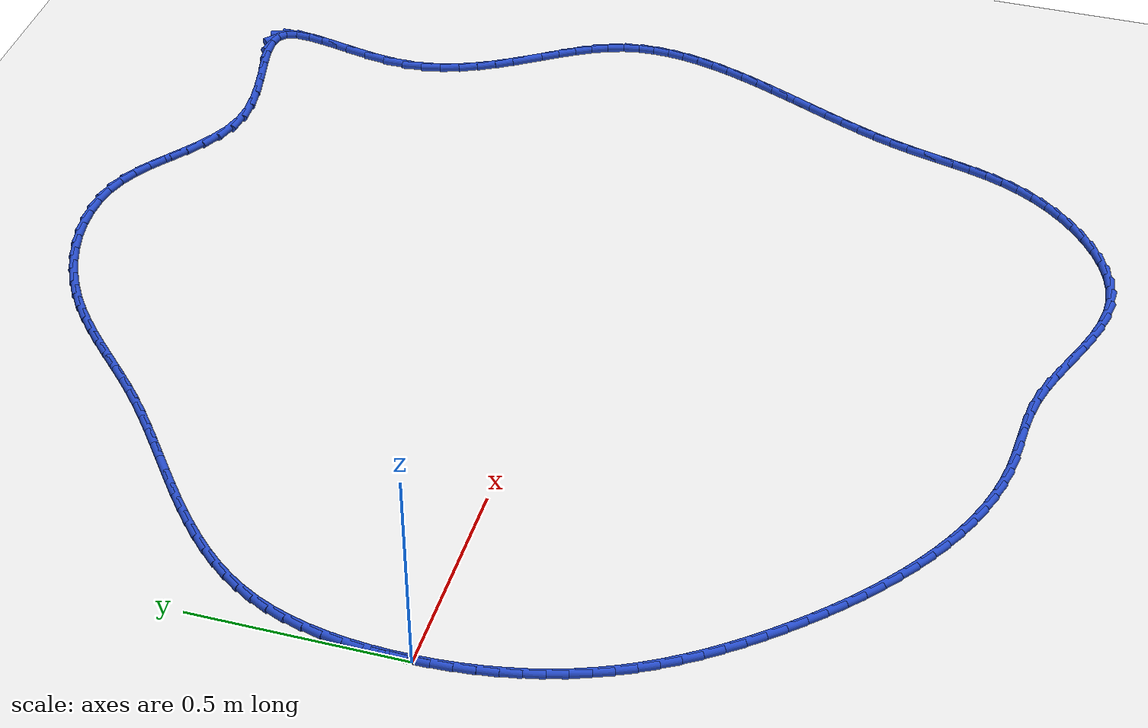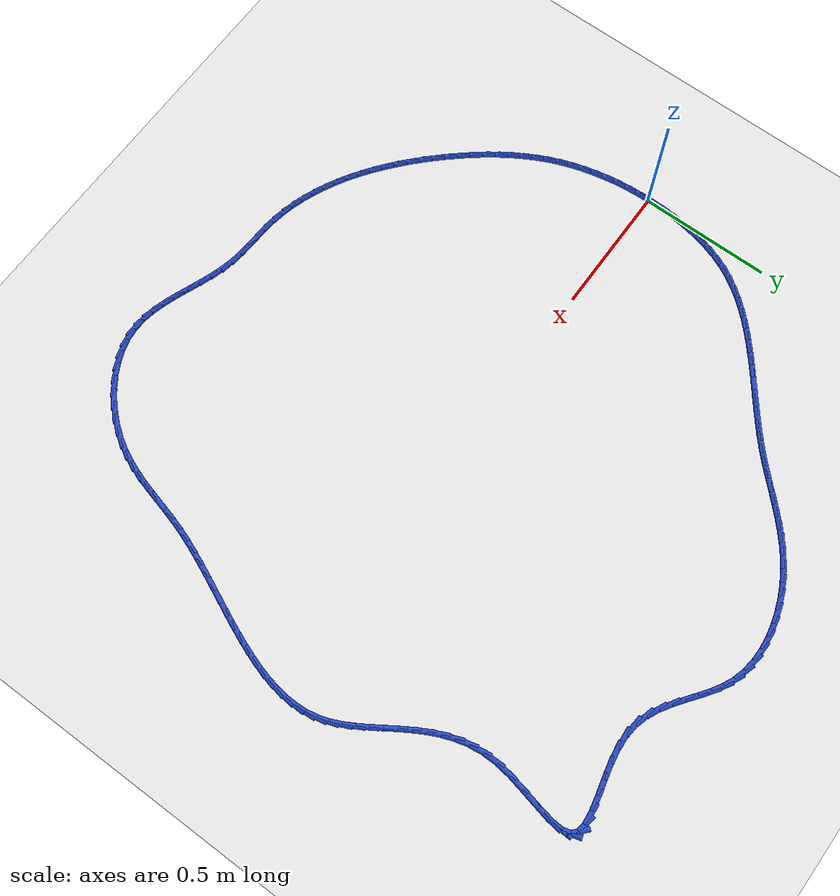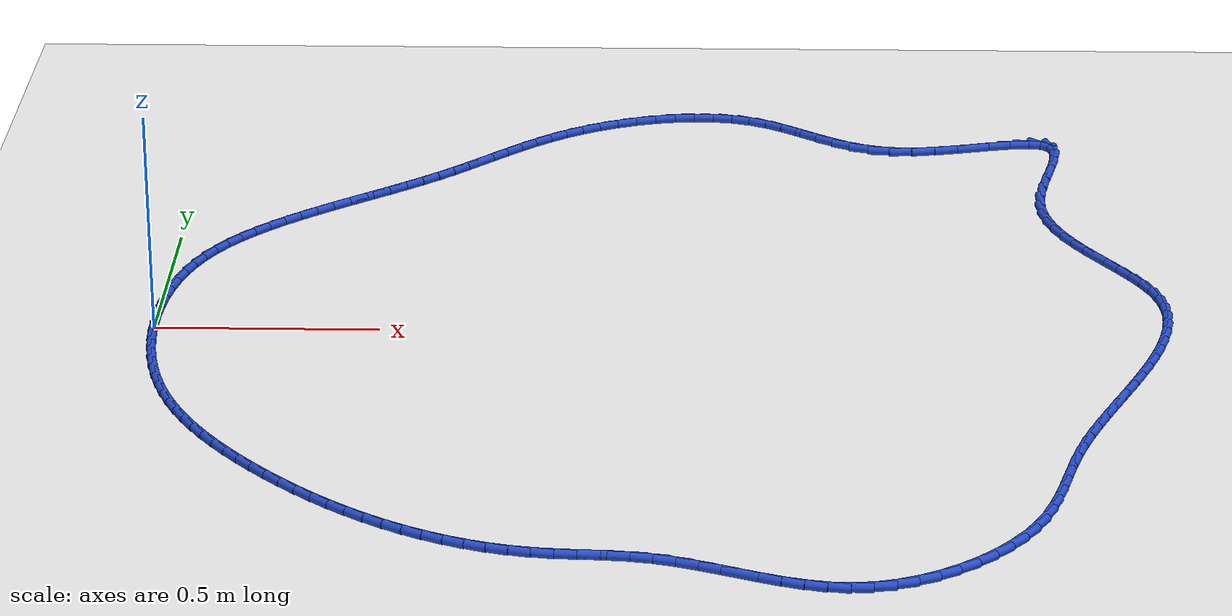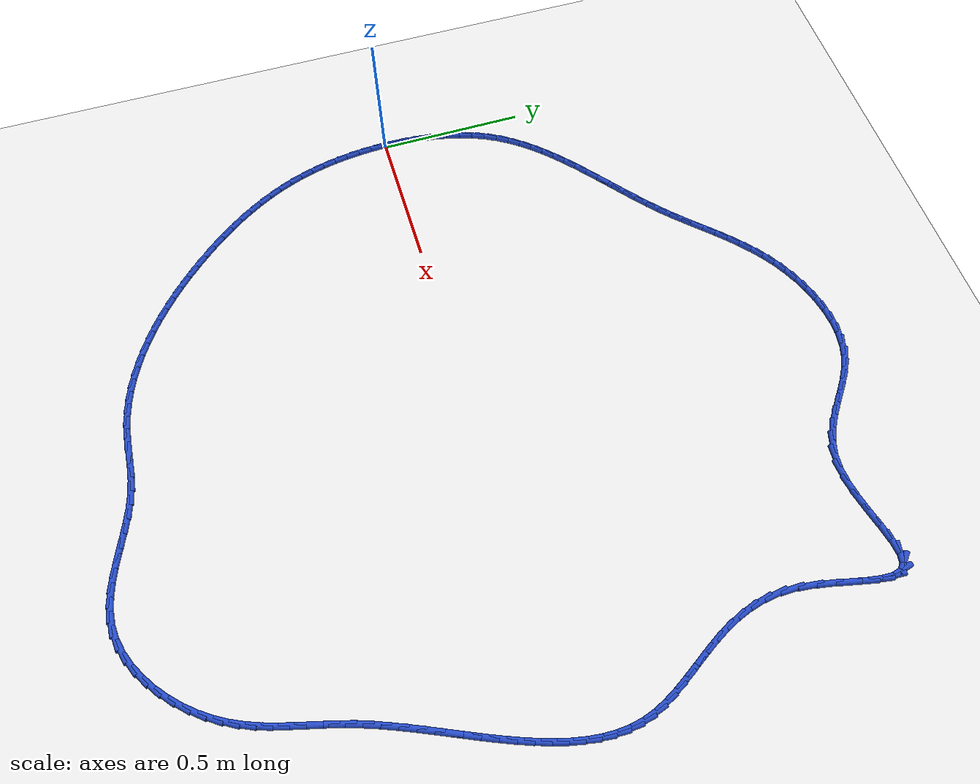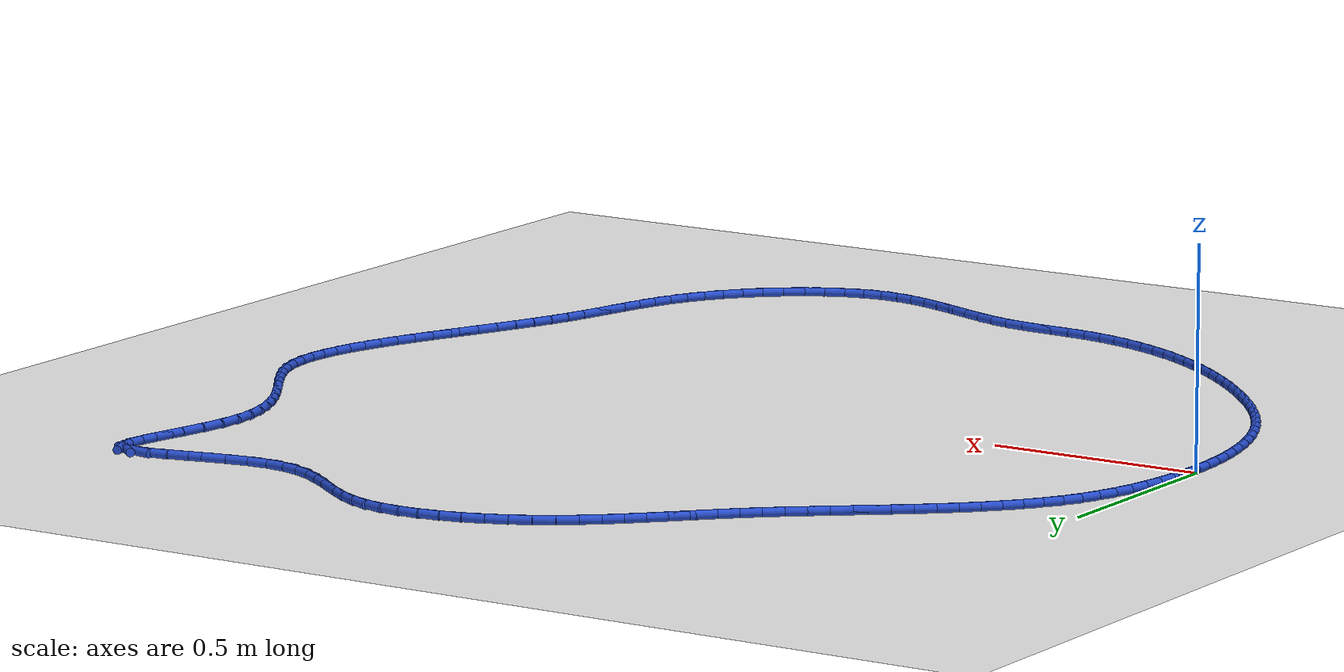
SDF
<sdf version="1.6">
 <world name="default">
  <light name="sun" type="directional">
   <pose>0 0 10 0 -0 0</pose>
   <diffuse>0.8 0.8 0.8 1</diffuse>
   <specular>0.2 0.2 0.2 1</specular>
   <attenuation>
    <range>1000</range>
    <constant>0.9</constant>
    <linear>0.01</linear>
    <quadratic>0.001</quadratic>
   </attenuation>
   <direction>-0.5 0.1 -0.9</direction>
  </light>
  <model name="ground_plane">
   <static>1</static>
   <link name="link">
    <collision name="collision">
     <geometry><plane><normal>0 0 1</normal><size>100 100</size></plane></geometry>
     <surface><friction><ode><mu>100</mu><mu2>50</mu2></ode></friction></surface>
    </collision>
    <visual name="visual">
     <cast_shadows>0</cast_shadows>
     <geometry><plane><normal>0 0 1</normal><size>100 100</size></plane></geometry>
     <material>
      <script><uri>file://media/materials/scripts/gazebo.material</uri><name>Gazebo/WhiteGlow</name></script>
     </material>
    </visual>
   </link>
  </model>
  <gravity>0 0 -9.8</gravity>
  <magnetic_field>6e-06 2.3e-05 -4.2e-05</magnetic_field>
  <atmosphere type="adiabatic"/>
  <physics name="default_physics" default="0" type="ode">
   <max_step_size>0.001</max_step_size>
   <real_time_factor>1</real_time_factor>
   <real_time_update_rate>1000</real_time_update_rate>
  </physics>
  <scene><ambient>0.4 0.4 0.4 1</ambient><background>0.7 0.7 0.7 1</background><shadows>1</shadows></scene>
  <spherical_coordinates>
   <surface_model>EARTH_WGS84</surface_model>
   <latitude_deg>0</latitude_deg>
   <longitude_deg>0</longitude_deg>
   <elevation>0</elevation>
   <heading_deg>0</heading_deg>
  </spherical_coordinates>
  <model name="line">
   <link name="link_0">
    <pose>4.5102810375396984e-17 4.163336342344337e-17 0.01 0 1.57 1.5652334050064227</pose>
    <collision name="collision">
     <geometry><cylinder><radius>0.01</radius><length>0.08</length></cylinder></geometry>
    </collision>
    <visual name="visual">
     <material>
      <script><name>Gazebo/Blue</name><uri>file://media/materials/scripts/gazebo.material</uri></script>
     </material>
     <geometry><cylinder><radius>0.01</radius><length>0.08</length></cylinder></geometry>
    </visual>
   </link>
   <link name="link_1">
    <pose>0.0002659733554597218 0.04781131605921755 0.01 0 1.57 1.5226781634985618</pose>
    <collision name="collision">
     <geometry><cylinder><radius>0.01</radius><length>0.08</length></cylinder></geometry>
    </collision>
    <visual name="visual">
     <material>
      <script><name>Gazebo/Blue</name><uri>file://media/materials/scripts/gazebo.material</uri></script>
     </material>
     <geometry><cylinder><radius>0.01</radius><length>0.08</length></cylinder></geometry>
    </visual>
   </link>
   <link name="link_2">
    <pose>0.00256746964531114 0.09560449010683651 0.01 0 1.57 1.4763867543394842</pose>
    <collision name="collision">
     <geometry><cylinder><radius>0.01</radius><length>0.08</length></cylinder></geometry>
    </collision>
    <visual name="visual">
     <material>
      <script><name>Gazebo/Blue</name><uri>file://media/materials/scripts/gazebo.material</uri></script>
     </material>
     <geometry><cylinder><radius>0.01</radius><length>0.08</length></cylinder></geometry>
    </visual>
   </link>
   <link name="link_3">
    <pose>0.007065199851168378 0.1431034791887835 0.01 0 1.57 1.4257564595323668</pose>
    <collision name="collision">
     <geometry><cylinder><radius>0.01</radius><length>0.08</length></cylinder></geometry>
    </collision>
    <visual name="visual">
     <material>
      <script><name>Gazebo/Blue</name><uri>file://media/materials/scripts/gazebo.material</uri></script>
     </material>
     <geometry><cylinder><radius>0.01</radius><length>0.08</length></cylinder></geometry>
    </visual>
   </link>
   <link name="link_4">
    <pose>0.013919874954645504 0.1900322403509849 0.01 0 1.57 1.3701513452137462</pose>
    <collision name="collision">
     <geometry><cylinder><radius>0.01</radius><length>0.08</length></cylinder></geometry>
    </collision>
    <visual name="visual">
     <material>
      <script><name>Gazebo/Blue</name><uri>file://media/materials/scripts/gazebo.material</uri></script>
     </material>
     <geometry><cylinder><radius>0.01</radius><length>0.08</length></cylinder></geometry>
    </visual>
   </link>
   <link name="link_5">
    <pose>0.0232922059373566 0.23611473063936744 0.01 0 1.57 1.308921094758801</pose>
    <collision name="collision">
     <geometry><cylinder><radius>0.01</radius><length>0.08</length></cylinder></geometry>
    </collision>
    <visual name="visual">
     <material>
      <script><name>Gazebo/Blue</name><uri>file://media/materials/scripts/gazebo.material</uri></script>
     </material>
     <geometry><cylinder><radius>0.01</radius><length>0.08</length></cylinder></geometry>
    </visual>
   </link>
   <link name="link_6">
    <pose>0.035342903780915744 0.2810749070998575 0.01 0 1.57 1.2414381184219754</pose>
    <collision name="collision">
     <geometry><cylinder><radius>0.01</radius><length>0.08</length></cylinder></geometry>
    </collision>
    <visual name="visual">
     <material>
      <script><name>Gazebo/Blue</name><uri>file://media/materials/scripts/gazebo.material</uri></script>
     </material>
     <geometry><cylinder><radius>0.01</radius><length>0.08</length></cylinder></geometry>
    </visual>
   </link>
   <link name="link_7">
    <pose>0.050232679466936984 0.3246367267783816 0.01 0 1.57 1.1671594621937802</pose>
    <collision name="collision">
     <geometry><cylinder><radius>0.01</radius><length>0.08</length></cylinder></geometry>
    </collision>
    <visual name="visual">
     <material>
      <script><name>Gazebo/Blue</name><uri>file://media/materials/scripts/gazebo.material</uri></script>
     </material>
     <geometry><cylinder><radius>0.01</radius><length>0.08</length></cylinder></geometry>
    </visual>
   </link>
   <link name="link_8">
    <pose>0.06812224397703441 0.3665241467208663 0.01 0 1.57 1.0862252213850343</pose>
    <collision name="collision">
     <geometry><cylinder><radius>0.01</radius><length>0.08</length></cylinder></geometry>
    </collision>
    <visual name="visual">
     <material>
      <script><name>Gazebo/Blue</name><uri>file://media/materials/scripts/gazebo.material</uri></script>
     </material>
     <geometry><cylinder><radius>0.01</radius><length>0.08</length></cylinder></geometry>
    </visual>
   </link>
   <link name="link_9">
    <pose>0.08915550299716676 0.40647830576742955 0.01 0 1.57 1.0063533597344037</pose>
    <collision name="collision">
     <geometry><cylinder><radius>0.01</radius><length>0.08</length></cylinder></geometry>
    </collision>
    <visual name="visual">
     <material>
      <script><name>Gazebo/Blue</name><uri>file://media/materials/scripts/gazebo.material</uri></script>
     </material>
     <geometry><cylinder><radius>0.01</radius><length>0.08</length></cylinder></geometry>
    </visual>
   </link>
   <link name="link_10">
    <pose>0.1132265105070675 0.4444957920333901 0.01 0 1.57 0.9342763934615821</pose>
    <collision name="collision">
     <geometry><cylinder><radius>0.01</radius><length>0.08</length></cylinder></geometry>
    </collision>
    <visual name="visual">
     <material>
      <script><name>Gazebo/Blue</name><uri>file://media/materials/scripts/gazebo.material</uri></script>
     </material>
     <geometry><cylinder><radius>0.01</radius><length>0.08</length></cylinder></geometry>
    </visual>
   </link>
   <link name="link_11">
    <pose>0.1400378018888805 0.4807690029310337 0.01 0 1.57 0.8708021590368316</pose>
    <collision name="collision">
     <geometry><cylinder><radius>0.01</radius><length>0.08</length></cylinder></geometry>
    </collision>
    <visual name="visual">
     <material>
      <script><name>Gazebo/Blue</name><uri>file://media/materials/scripts/gazebo.material</uri></script>
     </material>
     <geometry><cylinder><radius>0.01</radius><length>0.08</length></cylinder></geometry>
    </visual>
   </link>
   <link name="link_12">
    <pose>0.1692870330040851 0.5154953247119691 0.01 0 1.57 0.8161472947909374</pose>
    <collision name="collision">
     <geometry><cylinder><radius>0.01</radius><length>0.08</length></cylinder></geometry>
    </collision>
    <visual name="visual">
     <material>
      <script><name>Gazebo/Blue</name><uri>file://media/materials/scripts/gazebo.material</uri></script>
     </material>
     <geometry><cylinder><radius>0.01</radius><length>0.08</length></cylinder></geometry>
    </visual>
   </link>
   <link name="link_13">
    <pose>0.20067185971416074 0.5488721436278053 0.01 0 1.57 0.7702200249914737</pose>
    <collision name="collision">
     <geometry><cylinder><radius>0.01</radius><length>0.08</length></cylinder></geometry>
    </collision>
    <visual name="visual">
     <material>
      <script><name>Gazebo/Blue</name><uri>file://media/materials/scripts/gazebo.material</uri></script>
     </material>
     <geometry><cylinder><radius>0.01</radius><length>0.08</length></cylinder></geometry>
    </visual>
   </link>
   <link name="link_14">
    <pose>0.23388993788058682 0.5810968459301515 0.01 0 1.57 0.7327496721935243</pose>
    <collision name="collision">
     <geometry><cylinder><radius>0.01</radius><length>0.08</length></cylinder></geometry>
    </collision>
    <visual name="visual">
     <material>
      <script><name>Gazebo/Blue</name><uri>file://media/materials/scripts/gazebo.material</uri></script>
     </material>
     <geometry><cylinder><radius>0.01</radius><length>0.08</length></cylinder></geometry>
    </visual>
   </link>
   <link name="link_15">
    <pose>0.2686389233648427 0.6123668178706162 0.01 0 1.57 0.7033910940298831</pose>
    <collision name="collision">
     <geometry><cylinder><radius>0.01</radius><length>0.08</length></cylinder></geometry>
    </collision>
    <visual name="visual">
     <material>
      <script><name>Gazebo/Blue</name><uri>file://media/materials/scripts/gazebo.material</uri></script>
     </material>
     <geometry><cylinder><radius>0.01</radius><length>0.08</length></cylinder></geometry>
    </visual>
   </link>
   <link name="link_16">
    <pose>0.3046164720284079 0.6428794457008087 0.01 0 1.57 0.6817998807367432</pose>
    <collision name="collision">
     <geometry><cylinder><radius>0.01</radius><length>0.08</length></cylinder></geometry>
    </collision>
    <visual name="visual">
     <material>
      <script><name>Gazebo/Blue</name><uri>file://media/materials/scripts/gazebo.material</uri></script>
     </material>
     <geometry><cylinder><radius>0.01</radius><length>0.08</length></cylinder></geometry>
    </visual>
   </link>
   <link name="link_17">
    <pose>0.34152023973276174 0.6728321156723378 0.01 0 1.57 0.6676819469219742</pose>
    <collision name="collision">
     <geometry><cylinder><radius>0.01</radius><length>0.08</length></cylinder></geometry>
    </collision>
    <visual name="visual">
     <material>
      <script><name>Gazebo/Blue</name><uri>file://media/materials/scripts/gazebo.material</uri></script>
     </material>
     <geometry><cylinder><radius>0.01</radius><length>0.08</length></cylinder></geometry>
    </visual>
   </link>
   <link name="link_18">
    <pose>0.37904788233938375 0.7024222140368128 0.01 0 1.57 0.6608236430765778</pose>
    <collision name="collision">
     <geometry><cylinder><radius>0.01</radius><length>0.08</length></cylinder></geometry>
    </collision>
    <visual name="visual">
     <material>
      <script><name>Gazebo/Blue</name><uri>file://media/materials/scripts/gazebo.material</uri></script>
     </material>
     <geometry><cylinder><radius>0.01</radius><length>0.08</length></cylinder></geometry>
    </visual>
   </link>
   <link name="link_19">
    <pose>0.4168970557097531 0.7318471270458419 0.01 0 1.57 0.6611080759831992</pose>
    <collision name="collision">
     <geometry><cylinder><radius>0.01</radius><length>0.08</length></cylinder></geometry>
    </collision>
    <visual name="visual">
     <material>
      <script><name>Gazebo/Blue</name><uri>file://media/materials/scripts/gazebo.material</uri></script>
     </material>
     <geometry><cylinder><radius>0.01</radius><length>0.08</length></cylinder></geometry>
    </visual>
   </link>
   <link name="link_20">
    <pose>0.45476541570534956 0.7613042409510349 0.01 0 1.57 0.6685216754027642</pose>
    <collision name="collision">
     <geometry><cylinder><radius>0.01</radius><length>0.08</length></cylinder></geometry>
    </collision>
    <visual name="visual">
     <material>
      <script><name>Gazebo/Blue</name><uri>file://media/materials/scripts/gazebo.material</uri></script>
     </material>
     <geometry><cylinder><radius>0.01</radius><length>0.08</length></cylinder></geometry>
    </visual>
   </link>
   <link name="link_21">
    <pose>0.4923506181876522 0.7909909420040002 0.01 0 1.57 0.6831530600610272</pose>
    <collision name="collision">
     <geometry><cylinder><radius>0.01</radius><length>0.08</length></cylinder></geometry>
    </collision>
    <visual name="visual">
     <material>
      <script><name>Gazebo/Blue</name><uri>file://media/materials/scripts/gazebo.material</uri></script>
     </material>
     <geometry><cylinder><radius>0.01</radius><length>0.08</length></cylinder></geometry>
    </visual>
   </link>
   <link name="link_22">
    <pose>0.5293503190181407 0.8211046164563471 0.01 0 1.57 0.7051842614717638</pose>
    <collision name="collision">
     <geometry><cylinder><radius>0.01</radius><length>0.08</length></cylinder></geometry>
    </collision>
    <visual name="visual">
     <material>
      <script><name>Gazebo/Blue</name><uri>file://media/materials/scripts/gazebo.material</uri></script>
     </material>
     <geometry><cylinder><radius>0.01</radius><length>0.08</length></cylinder></geometry>
    </visual>
   </link>
   <link name="link_23">
    <pose>0.5654621740582942 0.8518426505596842 0.01 0 1.57 0.734805967708609</pose>
    <collision name="collision">
     <geometry><cylinder><radius>0.01</radius><length>0.08</length></cylinder></geometry>
    </collision>
    <visual name="visual">
     <material>
      <script><name>Gazebo/Blue</name><uri>file://media/materials/scripts/gazebo.material</uri></script>
     </material>
     <geometry><cylinder><radius>0.01</radius><length>0.08</length></cylinder></geometry>
    </visual>
   </link>
   <link name="link_24">
    <pose>0.6003863924385744 0.8834005214454815 0.01 0 1.57 0.7656476291308478</pose>
    <collision name="collision">
     <geometry><cylinder><radius>0.01</radius><length>0.08</length></cylinder></geometry>
    </collision>
    <visual name="visual">
     <material>
      <script><name>Gazebo/Blue</name><uri>file://media/materials/scripts/gazebo.material</uri></script>
     </material>
     <geometry><cylinder><radius>0.01</radius><length>0.08</length></cylinder></geometry>
    </visual>
   </link>
   <link name="link_25">
    <pose>0.6340758300660155 0.915784798201178 0.01 0 1.57 0.7854069243086584</pose>
    <collision name="collision">
     <geometry><cylinder><radius>0.01</radius><length>0.08</length></cylinder></geometry>
    </collision>
    <visual name="visual">
     <material>
      <script><name>Gazebo/Blue</name><uri>file://media/materials/scripts/gazebo.material</uri></script>
     </material>
     <geometry><cylinder><radius>0.01</radius><length>0.08</length></cylinder></geometry>
    </visual>
   </link>
   <link name="link_26">
    <pose>0.666946325942634 0.948655870033834 0.01 0 1.57 0.7924869824892709</pose>
    <collision name="collision">
     <geometry><cylinder><radius>0.01</radius><length>0.08</length></cylinder></geometry>
    </collision>
    <visual name="visual">
     <material>
      <script><name>Gazebo/Blue</name><uri>file://media/materials/scripts/gazebo.material</uri></script>
     </material>
     <geometry><cylinder><radius>0.01</radius><length>0.08</length></cylinder></geometry>
    </visual>
   </link>
   <link name="link_27">
    <pose>0.6994632412606615 0.9816370976151919 0.01 0 1.57 0.7867150209191134</pose>
    <collision name="collision">
     <geometry><cylinder><radius>0.01</radius><length>0.08</length></cylinder></geometry>
    </collision>
    <visual name="visual">
     <material>
      <script><name>Gazebo/Blue</name><uri>file://media/materials/scripts/gazebo.material</uri></script>
     </material>
     <geometry><cylinder><radius>0.01</radius><length>0.08</length></cylinder></geometry>
    </visual>
   </link>
   <link name="link_28">
    <pose>0.7320919372123287 1.0143518416169923 0.01 0 1.57 0.768024592440862</pose>
    <collision name="collision">
     <geometry><cylinder><radius>0.01</radius><length>0.08</length></cylinder></geometry>
    </collision>
    <visual name="visual">
     <material>
      <script><name>Gazebo/Blue</name><uri>file://media/materials/scripts/gazebo.material</uri></script>
     </material>
     <geometry><cylinder><radius>0.01</radius><length>0.08</length></cylinder></geometry>
    </visual>
   </link>
   <link name="link_29">
    <pose>0.765297774989867 1.046423462710977 0.01 0 1.57 0.7364866359164092</pose>
    <collision name="collision">
     <geometry><cylinder><radius>0.01</radius><length>0.08</length></cylinder></geometry>
    </collision>
    <visual name="visual">
     <material>
      <script><name>Gazebo/Blue</name><uri>file://media/materials/scripts/gazebo.material</uri></script>
     </material>
     <geometry><cylinder><radius>0.01</radius><length>0.08</length></cylinder></geometry>
    </visual>
   </link>
   <link name="link_30">
    <pose>0.7995461157855076 1.0774753215688873 0.01 0 1.57 0.6924002227723915</pose>
    <collision name="collision">
     <geometry><cylinder><radius>0.01</radius><length>0.08</length></cylinder></geometry>
    </collision>
    <visual name="visual">
     <material>
      <script><name>Gazebo/Blue</name><uri>file://media/materials/scripts/gazebo.material</uri></script>
     </material>
     <geometry><cylinder><radius>0.01</radius><length>0.08</length></cylinder></geometry>
    </visual>
   </link>
   <link name="link_31">
    <pose>0.835302320791482 1.1071307788624642 0.01 0 1.57 0.636430155390488</pose>
    <collision name="collision">
     <geometry><cylinder><radius>0.01</radius><length>0.08</length></cylinder></geometry>
    </collision>
    <visual name="visual">
     <material>
      <script><name>Gazebo/Blue</name><uri>file://media/materials/scripts/gazebo.material</uri></script>
     </material>
     <geometry><cylinder><radius>0.01</radius><length>0.08</length></cylinder></geometry>
    </visual>
   </link>
   <link name="link_32">
    <pose>0.8730317512000214 1.13501319526345 0.01 0 1.57 0.5697586324176485</pose>
    <collision name="collision">
     <geometry><cylinder><radius>0.01</radius><length>0.08</length></cylinder></geometry>
    </collision>
    <visual name="visual">
     <material>
      <script><name>Gazebo/Blue</name><uri>file://media/materials/scripts/gazebo.material</uri></script>
     </material>
     <geometry><cylinder><radius>0.01</radius><length>0.08</length></cylinder></geometry>
    </visual>
   </link>
   <link name="link_33">
    <pose>0.9131997276270933 1.1607459286052477 0.01 0 1.57 0.4960123316242508</pose>
    <collision name="collision">
     <geometry><cylinder><radius>0.01</radius><length>0.08</length></cylinder></geometry>
    </collision>
    <visual name="visual">
     <material>
      <script><name>Gazebo/Blue</name><uri>file://media/materials/scripts/gazebo.material</uri></script>
     </material>
     <geometry><cylinder><radius>0.01</radius><length>0.08</length></cylinder></geometry>
    </visual>
   </link>
   <link name="link_34">
    <pose>0.9560565505196716 1.1839372959159922 0.01 0 1.57 0.42142639953195427</pose>
    <collision name="collision">
     <geometry><cylinder><radius>0.01</radius><length>0.08</length></cylinder></geometry>
    </collision>
    <visual name="visual">
     <material>
      <script><name>Gazebo/Blue</name><uri>file://media/materials/scripts/gazebo.material</uri></script>
     </material>
     <geometry><cylinder><radius>0.01</radius><length>0.08</length></cylinder></geometry>
    </visual>
   </link>
   <link name="link_35">
    <pose>1.0011354152099636 1.2041454522392867 0.01 0 1.57 0.3449131976924875</pose>
    <collision name="collision">
     <geometry><cylinder><radius>0.01</radius><length>0.08</length></cylinder></geometry>
    </collision>
    <visual name="visual">
     <material>
      <script><name>Gazebo/Blue</name><uri>file://media/materials/scripts/gazebo.material</uri></script>
     </material>
     <geometry><cylinder><radius>0.01</radius><length>0.08</length></cylinder></geometry>
    </visual>
   </link>
   <link name="link_36">
    <pose>1.0478202046586 1.2209181081180367 0.01 0 1.57 0.2639605904391192</pose>
    <collision name="collision">
     <geometry><cylinder><radius>0.01</radius><length>0.08</length></cylinder></geometry>
    </collision>
    <visual name="visual">
     <material>
      <script><name>Gazebo/Blue</name><uri>file://media/materials/scripts/gazebo.material</uri></script>
     </material>
     <geometry><cylinder><radius>0.01</radius><length>0.08</length></cylinder></geometry>
    </visual>
   </link>
   <link name="link_37">
    <pose>1.0954948018262092 1.2338029740951473 0.01 0 1.57 0.17599750182136695</pose>
    <collision name="collision">
     <geometry><cylinder><radius>0.01</radius><length>0.08</length></cylinder></geometry>
    </collision>
    <visual name="visual">
     <material>
      <script><name>Gazebo/Blue</name><uri>file://media/materials/scripts/gazebo.material</uri></script>
     </material>
     <geometry><cylinder><radius>0.01</radius><length>0.08</length></cylinder></geometry>
    </visual>
   </link>
   <link name="link_38">
    <pose>1.143543089673421 1.2423477607135238 0.01 0 1.57 0.07833223116335455</pose>
    <collision name="collision">
     <geometry><cylinder><radius>0.01</radius><length>0.08</length></cylinder></geometry>
    </collision>
    <visual name="visual">
     <material>
      <script><name>Gazebo/Blue</name><uri>file://media/materials/scripts/gazebo.material</uri></script>
     </material>
     <geometry><cylinder><radius>0.01</radius><length>0.08</length></cylinder></geometry>
    </visual>
   </link>
   <link name="link_39">
    <pose>1.1913489511608648 1.24610017851607 0.01 0 1.57 -0.031774727334678725</pose>
    <collision name="collision">
     <geometry><cylinder><radius>0.01</radius><length>0.08</length></cylinder></geometry>
    </collision>
    <visual name="visual">
     <material>
      <script><name>Gazebo/Blue</name><uri>file://media/materials/scripts/gazebo.material</uri></script>
     </material>
     <geometry><cylinder><radius>0.01</radius><length>0.08</length></cylinder></geometry>
    </visual>
   </link>
   <link name="link_40">
    <pose>1.2382962692491697 1.2446079380456914 0.01 0 1.57 -0.1568013047305751</pose>
    <collision name="collision">
     <geometry><cylinder><radius>0.01</radius><length>0.08</length></cylinder></geometry>
    </collision>
    <visual name="visual">
     <material>
      <script><name>Gazebo/Blue</name><uri>file://media/materials/scripts/gazebo.material</uri></script>
     </material>
     <geometry><cylinder><radius>0.01</radius><length>0.08</length></cylinder></geometry>
    </visual>
   </link>
   <link name="link_41">
    <pose>1.283768926898966 1.237418749845293 0.01 0 1.57 -0.29829159822095574</pose>
    <collision name="collision">
     <geometry><cylinder><radius>0.01</radius><length>0.08</length></cylinder></geometry>
    </collision>
    <visual name="visual">
     <material>
      <script><name>Gazebo/Blue</name><uri>file://media/materials/scripts/gazebo.material</uri></script>
     </material>
     <geometry><cylinder><radius>0.01</radius><length>0.08</length></cylinder></geometry>
    </visual>
   </link>
   <link name="link_42">
    <pose>1.3271508070708824 1.2240803244577803 0.01 0 1.57 -0.4475374454338112</pose>
    <collision name="collision">
     <geometry><cylinder><radius>0.01</radius><length>0.08</length></cylinder></geometry>
    </collision>
    <visual name="visual">
     <material>
      <script><name>Gazebo/Blue</name><uri>file://media/materials/scripts/gazebo.material</uri></script>
     </material>
     <geometry><cylinder><radius>0.01</radius><length>0.08</length></cylinder></geometry>
    </visual>
   </link>
   <link name="link_43">
    <pose>1.3680267707840656 1.2044589832217336 0.01 0 1.57 -0.5607190232727151</pose>
    <collision name="collision">
     <geometry><cylinder><radius>0.01</radius><length>0.08</length></cylinder></geometry>
    </collision>
    <visual name="visual">
     <material>
      <script><name>Gazebo/Blue</name><uri>file://media/materials/scripts/gazebo.material</uri></script>
     </material>
     <geometry><cylinder><radius>0.01</radius><length>0.08</length></cylinder></geometry>
    </visual>
   </link>
   <link name="link_44">
    <pose>1.4069775385761374 1.1799997849553465 0.01 0 1.57 -0.6251632926310164</pose>
    <collision name="collision">
     <geometry><cylinder><radius>0.01</radius><length>0.08</length></cylinder></geometry>
    </collision>
    <visual name="visual">
     <material>
      <script><name>Gazebo/Blue</name><uri>file://media/materials/scripts/gazebo.material</uri></script>
     </material>
     <geometry><cylinder><radius>0.01</radius><length>0.08</length></cylinder></geometry>
    </visual>
   </link>
   <link name="link_45">
    <pose>1.444891716823267 1.152635880324854 0.01 0 1.57 -0.6436807654438337</pose>
    <collision name="collision">
     <geometry><cylinder><radius>0.01</radius><length>0.08</length></cylinder></geometry>
    </collision>
    <visual name="visual">
     <material>
      <script><name>Gazebo/Blue</name><uri>file://media/materials/scripts/gazebo.material</uri></script>
     </material>
     <geometry><cylinder><radius>0.01</radius><length>0.08</length></cylinder></geometry>
    </visual>
   </link>
   <link name="link_46">
    <pose>1.4826580022899651 1.1243005632892524 0.01 0 1.57 -0.6179823619485597</pose>
    <collision name="collision">
     <geometry><cylinder><radius>0.01</radius><length>0.08</length></cylinder></geometry>
    </collision>
    <visual name="visual">
     <material>
      <script><name>Gazebo/Blue</name><uri>file://media/materials/scripts/gazebo.material</uri></script>
     </material>
     <geometry><cylinder><radius>0.01</radius><length>0.08</length></cylinder></geometry>
    </visual>
   </link>
   <link name="link_47">
    <pose>1.5211650917407433 1.0969271278075403 0.01 0 1.57 -0.5476481269111763</pose>
    <collision name="collision">
     <geometry><cylinder><radius>0.01</radius><length>0.08</length></cylinder></geometry>
    </collision>
    <visual name="visual">
     <material>
      <script><name>Gazebo/Blue</name><uri>file://media/materials/scripts/gazebo.material</uri></script>
     </material>
     <geometry><cylinder><radius>0.01</radius><length>0.08</length></cylinder></geometry>
    </visual>
   </link>
   <link name="link_48">
    <pose>1.5613016819401115 1.0724488678387132 0.01 0 1.57 -0.4316917704125591</pose>
    <collision name="collision">
     <geometry><cylinder><radius>0.01</radius><length>0.08</length></cylinder></geometry>
    </collision>
    <visual name="visual">
     <material>
      <script><name>Gazebo/Blue</name><uri>file://media/materials/scripts/gazebo.material</uri></script>
     </material>
     <geometry><cylinder><radius>0.01</radius><length>0.08</length></cylinder></geometry>
    </visual>
   </link>
   <link name="link_49">
    <pose>1.603956469652582 1.0527990773417697 0.01 0 1.57 -0.27282259820011046</pose>
    <collision name="collision">
     <geometry><cylinder><radius>0.01</radius><length>0.08</length></cylinder></geometry>
    </collision>
    <visual name="visual">
     <material>
      <script><name>Gazebo/Blue</name><uri>file://media/materials/scripts/gazebo.material</uri></script>
     </material>
     <geometry><cylinder><radius>0.01</radius><length>0.08</length></cylinder></geometry>
    </visual>
   </link>
   <link name="link_50">
    <pose>1.6500181516426642 1.0399110502757052 0.01 0 1.57 -0.08451036166621988</pose>
    <collision name="collision">
     <geometry><cylinder><radius>0.01</radius><length>0.08</length></cylinder></geometry>
    </collision>
    <visual name="visual">
     <material>
      <script><name>Gazebo/Blue</name><uri>file://media/materials/scripts/gazebo.material</uri></script>
     </material>
     <geometry><cylinder><radius>0.01</radius><length>0.08</length></cylinder></geometry>
    </visual>
   </link>
   <link name="link_51">
    <pose>1.7003308070543601 1.0356489581135537 0.01 0 1.57 0.07581926381912904</pose>
    <collision name="collision">
     <geometry><cylinder><radius>0.01</radius><length>0.08</length></cylinder></geometry>
    </collision>
    <visual name="visual">
     <material>
      <script><name>Gazebo/Blue</name><uri>file://media/materials/scripts/gazebo.material</uri></script>
     </material>
     <geometry><cylinder><radius>0.01</radius><length>0.08</length></cylinder></geometry>
    </visual>
   </link>
   <link name="link_52">
    <pose>1.7543680973071665 1.0397538945208913 0.01 0 1.57 0.17334936584459137</pose>
    <collision name="collision">
     <geometry><cylinder><radius>0.01</radius><length>0.08</length></cylinder></geometry>
    </collision>
    <visual name="visual">
     <material>
      <script><name>Gazebo/Blue</name><uri>file://media/materials/scripts/gazebo.material</uri></script>
     </material>
     <geometry><cylinder><radius>0.01</radius><length>0.08</length></cylinder></geometry>
    </visual>
   </link>
   <link name="link_53">
    <pose>1.810009408464629 1.0494970707568727 0.01 0 1.57 0.22357490172900715</pose>
    <collision name="collision">
     <geometry><cylinder><radius>0.01</radius><length>0.08</length></cylinder></geometry>
    </collision>
    <visual name="visual">
     <material>
      <script><name>Gazebo/Blue</name><uri>file://media/materials/scripts/gazebo.material</uri></script>
     </material>
     <geometry><cylinder><radius>0.01</radius><length>0.08</length></cylinder></geometry>
    </visual>
   </link>
   <link name="link_54">
    <pose>1.8650444159001893 1.0620107165337538 0.01 0 1.57 0.23344227509720847</pose>
    <collision name="collision">
     <geometry><cylinder><radius>0.01</radius><length>0.08</length></cylinder></geometry>
    </collision>
    <visual name="visual">
     <material>
      <script><name>Gazebo/Blue</name><uri>file://media/materials/scripts/gazebo.material</uri></script>
     </material>
     <geometry><cylinder><radius>0.01</radius><length>0.08</length></cylinder></geometry>
    </visual>
   </link>
   <link name="link_55">
    <pose>1.9172627949872918 1.074427061563792 0.01 0 1.57 0.19766019570771223</pose>
    <collision name="collision">
     <geometry><cylinder><radius>0.01</radius><length>0.08</length></cylinder></geometry>
    </collision>
    <visual name="visual">
     <material>
      <script><name>Gazebo/Blue</name><uri>file://media/materials/scripts/gazebo.material</uri></script>
     </material>
     <geometry><cylinder><radius>0.01</radius><length>0.08</length></cylinder></geometry>
    </visual>
   </link>
   <link name="link_56">
    <pose>1.9644542210993792 1.0838783355592445 0.01 0 1.57 0.09031823905235421</pose>
    <collision name="collision">
     <geometry><cylinder><radius>0.01</radius><length>0.08</length></cylinder></geometry>
    </collision>
    <visual name="visual">
     <material>
      <script><name>Gazebo/Blue</name><uri>file://media/materials/scripts/gazebo.material</uri></script>
     </material>
     <geometry><cylinder><radius>0.01</radius><length>0.08</length></cylinder></geometry>
    </visual>
   </link>
   <link name="link_57">
    <pose>2.0044083696098935 1.0874967682323673 0.01 0 1.57 -0.16507706059372845</pose>
    <collision name="collision">
     <geometry><cylinder><radius>0.01</radius><length>0.08</length></cylinder></geometry>
    </collision>
    <visual name="visual">
     <material>
      <script><name>Gazebo/Blue</name><uri>file://media/materials/scripts/gazebo.material</uri></script>
     </material>
     <geometry><cylinder><radius>0.01</radius><length>0.08</length></cylinder></geometry>
    </visual>
   </link>
   <link name="link_58">
    <pose>2.034914915892279 1.082414589295418 0.01 0 1.57 -0.7193502826881091</pose>
    <collision name="collision">
     <geometry><cylinder><radius>0.01</radius><length>0.08</length></cylinder></geometry>
    </collision>
    <visual name="visual">
     <material>
      <script><name>Gazebo/Blue</name><uri>file://media/materials/scripts/gazebo.material</uri></script>
     </material>
     <geometry><cylinder><radius>0.01</radius><length>0.08</length></cylinder></geometry>
    </visual>
   </link>
   <link name="link_59">
    <pose>2.053837443026246 1.065839987432087 0.01 0 1.57 -1.3179193909703175</pose>
    <collision name="collision">
     <geometry><cylinder><radius>0.01</radius><length>0.08</length></cylinder></geometry>
    </collision>
    <visual name="visual">
     <material>
      <script><name>Gazebo/Blue</name><uri>file://media/materials/scripts/gazebo.material</uri></script>
     </material>
     <geometry><cylinder><radius>0.01</radius><length>0.08</length></cylinder></geometry>
    </visual>
   </link>
   <link name="link_60">
    <pose>2.0612299123886766 1.0372323222919402 0.01 0 1.57 1.5298909134646828</pose>
    <collision name="collision">
     <geometry><cylinder><radius>0.01</radius><length>0.08</length></cylinder></geometry>
    </collision>
    <visual name="visual">
     <material>
      <script><name>Gazebo/Blue</name><uri>file://media/materials/scripts/gazebo.material</uri></script>
     </material>
     <geometry><cylinder><radius>0.01</radius><length>0.08</length></cylinder></geometry>
    </visual>
   </link>
   <link name="link_61">
    <pose>2.059649736940004 0.9986238869427719 0.01 0 1.57 1.4031519282249263</pose>
    <collision name="collision">
     <geometry><cylinder><radius>0.01</radius><length>0.08</length></cylinder></geometry>
    </collision>
    <visual name="visual">
     <material>
      <script><name>Gazebo/Blue</name><uri>file://media/materials/scripts/gazebo.material</uri></script>
     </material>
     <geometry><cylinder><radius>0.01</radius><length>0.08</length></cylinder></geometry>
    </visual>
   </link>
   <link name="link_62">
    <pose>2.0517912025381 0.9521876461770461 0.01 0 1.57 1.3545652106312118</pose>
    <collision name="collision">
     <geometry><cylinder><radius>0.01</radius><length>0.08</length></cylinder></geometry>
    </collision>
    <visual name="visual">
     <material>
      <script><name>Gazebo/Blue</name><uri>file://media/materials/scripts/gazebo.material</uri></script>
     </material>
     <geometry><cylinder><radius>0.01</radius><length>0.08</length></cylinder></geometry>
    </visual>
   </link>
   <link name="link_63">
    <pose>2.0403485950408426 0.9000965647872247 0.01 0 1.57 1.3524215035014786</pose>
    <collision name="collision">
     <geometry><cylinder><radius>0.01</radius><length>0.08</length></cylinder></geometry>
    </collision>
    <visual name="visual">
     <material>
      <script><name>Gazebo/Blue</name><uri>file://media/materials/scripts/gazebo.material</uri></script>
     </material>
     <geometry><cylinder><radius>0.01</radius><length>0.08</length></cylinder></geometry>
    </visual>
   </link>
   <link name="link_64">
    <pose>2.0280162003061024 0.8445236075657706 0.01 0 1.57 1.387783810531977</pose>
    <collision name="collision">
     <geometry><cylinder><radius>0.01</radius><length>0.08</length></cylinder></geometry>
    </collision>
    <visual name="visual">
     <material>
      <script><name>Gazebo/Blue</name><uri>file://media/materials/scripts/gazebo.material</uri></script>
     </material>
     <geometry><cylinder><radius>0.01</radius><length>0.08</length></cylinder></geometry>
    </visual>
   </link>
   <link name="link_65">
    <pose>2.0174883041917555 0.7876417393051469 0.01 0 1.57 1.4635805779557667</pose>
    <collision name="collision">
     <geometry><cylinder><radius>0.01</radius><length>0.08</length></cylinder></geometry>
    </collision>
    <visual name="visual">
     <material>
      <script><name>Gazebo/Blue</name><uri>file://media/materials/scripts/gazebo.material</uri></script>
     </material>
     <geometry><cylinder><radius>0.01</radius><length>0.08</length></cylinder></geometry>
    </visual>
   </link>
   <link name="link_66">
    <pose>2.0114591925556757 0.7316239247978155 0.01 0 1.57 -1.5567681061077525</pose>
    <collision name="collision">
     <geometry><cylinder><radius>0.01</radius><length>0.08</length></cylinder></geometry>
    </collision>
    <visual name="visual">
     <material>
      <script><name>Gazebo/Blue</name><uri>file://media/materials/scripts/gazebo.material</uri></script>
     </material>
     <geometry><cylinder><radius>0.01</radius><length>0.08</length></cylinder></geometry>
    </visual>
   </link>
   <link name="link_67">
    <pose>2.01220641762891 0.6783615707518079 0.01 0 1.57 -1.4251010836758564</pose>
    <collision name="collision">
     <geometry><cylinder><radius>0.01</radius><length>0.08</length></cylinder></geometry>
    </collision>
    <visual name="visual">
     <material>
      <script><name>Gazebo/Blue</name><uri>file://media/materials/scripts/gazebo.material</uri></script>
     </material>
     <geometry><cylinder><radius>0.01</radius><length>0.08</length></cylinder></geometry>
    </visual>
   </link>
   <link name="link_68">
    <pose>2.0195806112070773 0.6281063816172126 0.01 0 1.57 -1.3046031992397633</pose>
    <collision name="collision">
     <geometry><cylinder><radius>0.01</radius><length>0.08</length></cylinder></geometry>
    </collision>
    <visual name="visual">
     <material>
      <script><name>Gazebo/Blue</name><uri>file://media/materials/scripts/gazebo.material</uri></script>
     </material>
     <geometry><cylinder><radius>0.01</radius><length>0.08</length></cylinder></geometry>
    </visual>
   </link>
   <link name="link_69">
    <pose>2.0325562244649222 0.5805180872076876 0.01 0 1.57 -1.2008990077252228</pose>
    <collision name="collision">
     <geometry><cylinder><radius>0.01</radius><length>0.08</length></cylinder></geometry>
    </collision>
    <visual name="visual">
     <material>
      <script><name>Gazebo/Blue</name><uri>file://media/materials/scripts/gazebo.material</uri></script>
     </material>
     <geometry><cylinder><radius>0.01</radius><length>0.08</length></cylinder></geometry>
    </visual>
   </link>
   <link name="link_70">
    <pose>2.0501065229782944 0.5352556163097301 0.01 0 1.57 -1.1171918811300094</pose>
    <collision name="collision">
     <geometry><cylinder><radius>0.01</radius><length>0.08</length></cylinder></geometry>
    </collision>
    <visual name="visual">
     <material>
      <script><name>Gazebo/Blue</name><uri>file://media/materials/scripts/gazebo.material</uri></script>
     </material>
     <geometry><cylinder><radius>0.01</radius><length>0.08</length></cylinder></geometry>
    </visual>
   </link>
   <link name="link_71">
    <pose>2.0712047723230467 0.49197789770983835 0.01 0 1.57 -1.0547594009220238</pose>
    <collision name="collision">
     <geometry><cylinder><radius>0.01</radius><length>0.08</length></cylinder></geometry>
    </collision>
    <visual name="visual">
     <material>
      <script><name>Gazebo/Blue</name><uri>file://media/materials/scripts/gazebo.material</uri></script>
     </material>
     <geometry><cylinder><radius>0.01</radius><length>0.08</length></cylinder></geometry>
    </visual>
   </link>
   <link name="link_72">
    <pose>2.0948242380750286 0.45034386019451117 0.01 0 1.57 -1.0138603770396462</pose>
    <collision name="collision">
     <geometry><cylinder><radius>0.01</radius><length>0.08</length></cylinder></geometry>
    </collision>
    <visual name="visual">
     <material>
      <script><name>Gazebo/Blue</name><uri>file://media/materials/scripts/gazebo.material</uri></script>
     </material>
     <geometry><cylinder><radius>0.01</radius><length>0.08</length></cylinder></geometry>
    </visual>
   </link>
   <link name="link_73">
    <pose>2.119938185810093 0.41001243255024583 0.01 0 1.57 -0.9945770501428814</pose>
    <collision name="collision">
     <geometry><cylinder><radius>0.01</radius><length>0.08</length></cylinder></geometry>
    </collision>
    <visual name="visual">
     <material>
      <script><name>Gazebo/Blue</name><uri>file://media/materials/scripts/gazebo.material</uri></script>
     </material>
     <geometry><cylinder><radius>0.01</radius><length>0.08</length></cylinder></geometry>
    </visual>
   </link>
   <link name="link_74">
    <pose>2.1455198811040894 0.37064254356354115 0.01 0 1.57 -0.9974097007514006</pose>
    <collision name="collision">
     <geometry><cylinder><radius>0.01</radius><length>0.08</length></cylinder></geometry>
    </collision>
    <visual name="visual">
     <material>
      <script><name>Gazebo/Blue</name><uri>file://media/materials/scripts/gazebo.material</uri></script>
     </material>
     <geometry><cylinder><radius>0.01</radius><length>0.08</length></cylinder></geometry>
    </visual>
   </link>
   <link name="link_75">
    <pose>2.170542589532871 0.3318931220208951 0.01 0 1.57 -1.0236197055445337</pose>
    <collision name="collision">
     <geometry><cylinder><radius>0.01</radius><length>0.08</length></cylinder></geometry>
    </collision>
    <visual name="visual">
     <material>
      <script><name>Gazebo/Blue</name><uri>file://media/materials/scripts/gazebo.material</uri></script>
     </material>
     <geometry><cylinder><radius>0.01</radius><length>0.08</length></cylinder></geometry>
    </visual>
   </link>
   <link name="link_76">
    <pose>2.193979576672289 0.2934230967088056 0.01 0 1.57 -1.0753132374164656</pose>
    <collision name="collision">
     <geometry><cylinder><radius>0.01</radius><length>0.08</length></cylinder></geometry>
    </collision>
    <visual name="visual">
     <material>
      <script><name>Gazebo/Blue</name><uri>file://media/materials/scripts/gazebo.material</uri></script>
     </material>
     <geometry><cylinder><radius>0.01</radius><length>0.08</length></cylinder></geometry>
    </visual>
   </link>
   <link name="link_77">
    <pose>2.2148041080981935 0.25489139641377107 0.01 0 1.57 -1.1551240872033282</pose>
    <collision name="collision">
     <geometry><cylinder><radius>0.01</radius><length>0.08</length></cylinder></geometry>
    </collision>
    <visual name="visual">
     <material>
      <script><name>Gazebo/Blue</name><uri>file://media/materials/scripts/gazebo.material</uri></script>
     </material>
     <geometry><cylinder><radius>0.01</radius><length>0.08</length></cylinder></geometry>
    </visual>
   </link>
   <link name="link_78">
    <pose>2.2319894493864356 0.21595694992228923 0.01 0 1.57 -1.2648229897269252</pose>
    <collision name="collision">
     <geometry><cylinder><radius>0.01</radius><length>0.08</length></cylinder></geometry>
    </collision>
    <visual name="visual">
     <material>
      <script><name>Gazebo/Blue</name><uri>file://media/materials/scripts/gazebo.material</uri></script>
     </material>
     <geometry><cylinder><radius>0.01</radius><length>0.08</length></cylinder></geometry>
    </visual>
   </link>
   <link name="link_79">
    <pose>2.244522351126211 0.176282479946444 0.01 0 1.57 -1.3892022795305812</pose>
    <collision name="collision">
     <geometry><cylinder><radius>0.01</radius><length>0.08</length></cylinder></geometry>
    </collision>
    <visual name="visual">
     <material>
      <script><name>Gazebo/Blue</name><uri>file://media/materials/scripts/gazebo.material</uri></script>
     </material>
     <geometry><cylinder><radius>0.01</radius><length>0.08</length></cylinder></geometry>
    </visual>
   </link>
   <link name="link_80">
    <pose>2.251974828024355 0.13569536965903792 0.01 0 1.57 -1.5047452914004007</pose>
    <collision name="collision">
     <geometry><cylinder><radius>0.01</radius><length>0.08</length></cylinder></geometry>
    </collision>
    <visual name="visual">
     <material>
      <script><name>Gazebo/Blue</name><uri>file://media/materials/scripts/gazebo.material</uri></script>
     </material>
     <geometry><cylinder><radius>0.01</radius><length>0.08</length></cylinder></geometry>
    </visual>
   </link>
   <link name="link_81">
    <pose>2.2547164973723257 0.09424740281561332 0.01 0 1.57 1.5343008374824036</pose>
    <collision name="collision">
     <geometry><cylinder><radius>0.01</radius><length>0.08</length></cylinder></geometry>
    </collision>
    <visual name="visual">
     <material>
      <script><name>Gazebo/Blue</name><uri>file://media/materials/scripts/gazebo.material</uri></script>
     </material>
     <geometry><cylinder><radius>0.01</radius><length>0.08</length></cylinder></geometry>
    </visual>
   </link>
   <link name="link_82">
    <pose>2.25317420888752 0.05200646516282919 0.01 0 1.57 1.4457849817697355</pose>
    <collision name="collision">
     <geometry><cylinder><radius>0.01</radius><length>0.08</length></cylinder></geometry>
    </collision>
    <visual name="visual">
     <material>
      <script><name>Gazebo/Blue</name><uri>file://media/materials/scripts/gazebo.material</uri></script>
     </material>
     <geometry><cylinder><radius>0.01</radius><length>0.08</length></cylinder></geometry>
    </visual>
   </link>
   <link name="link_83">
    <pose>2.2477748122873398 0.009040442447347093 0.01 0 1.57 1.3710872096856035</pose>
    <collision name="collision">
     <geometry><cylinder><radius>0.01</radius><length>0.08</length></cylinder></geometry>
    </collision>
    <visual name="visual">
     <material>
      <script><name>Gazebo/Blue</name><uri>file://media/materials/scripts/gazebo.material</uri></script>
     </material>
     <geometry><cylinder><radius>0.01</radius><length>0.08</length></cylinder></geometry>
    </visual>
   </link>
   <link name="link_84">
    <pose>2.2389451572891836 -0.03458277958417397 0.01 0 1.57 1.3092850059011312</pose>
    <collision name="collision">
     <geometry><cylinder><radius>0.01</radius><length>0.08</length></cylinder></geometry>
    </collision>
    <visual name="visual">
     <material>
      <script><name>Gazebo/Blue</name><uri>file://media/materials/scripts/gazebo.material</uri></script>
     </material>
     <geometry><cylinder><radius>0.01</radius><length>0.08</length></cylinder></geometry>
    </visual>
   </link>
   <link name="link_85">
    <pose>2.2271120936104505 -0.07879531518507388 0.01 0 1.57 1.2591731441745422</pose>
    <collision name="collision">
     <geometry><cylinder><radius>0.01</radius><length>0.08</length></cylinder></geometry>
    </collision>
    <visual name="visual">
     <material>
      <script><name>Gazebo/Blue</name><uri>file://media/materials/scripts/gazebo.material</uri></script>
     </material>
     <geometry><cylinder><radius>0.01</radius><length>0.08</length></cylinder></geometry>
    </visual>
   </link>
   <link name="link_86">
    <pose>2.212702470968541 -0.12352927860869284 0.01 0 1.57 1.219535306974952</pose>
    <collision name="collision">
     <geometry><cylinder><radius>0.01</radius><length>0.08</length></cylinder></geometry>
    </collision>
    <visual name="visual">
     <material>
      <script><name>Gazebo/Blue</name><uri>file://media/materials/scripts/gazebo.material</uri></script>
     </material>
     <geometry><cylinder><radius>0.01</radius><length>0.08</length></cylinder></geometry>
    </visual>
   </link>
   <link name="link_87">
    <pose>2.1961431390808532 -0.16871678410837168 0.01 0 1.57 1.1892891814576432</pose>
    <collision name="collision">
     <geometry><cylinder><radius>0.01</radius><length>0.08</length></cylinder></geometry>
    </collision>
    <visual name="visual">
     <material>
      <script><name>Gazebo/Blue</name><uri>file://media/materials/scripts/gazebo.material</uri></script>
     </material>
     <geometry><cylinder><radius>0.01</radius><length>0.08</length></cylinder></geometry>
    </visual>
   </link>
   <link name="link_88">
    <pose>2.1778609476647866 -0.21428994593744888 0.01 0 1.57 1.1675504236602035</pose>
    <collision name="collision">
     <geometry><cylinder><radius>0.01</radius><length>0.08</length></cylinder></geometry>
    </collision>
    <visual name="visual">
     <material>
      <script><name>Gazebo/Blue</name><uri>file://media/materials/scripts/gazebo.material</uri></script>
     </material>
     <geometry><cylinder><radius>0.01</radius><length>0.08</length></cylinder></geometry>
    </visual>
   </link>
   <link name="link_89">
    <pose>2.1582827464377425 -0.2601808783492654 0.01 0 1.57 1.1536523906364358</pose>
    <collision name="collision">
     <geometry><cylinder><radius>0.01</radius><length>0.08</length></cylinder></geometry>
    </collision>
    <visual name="visual">
     <material>
      <script><name>Gazebo/Blue</name><uri>file://media/materials/scripts/gazebo.material</uri></script>
     </material>
     <geometry><cylinder><radius>0.01</radius><length>0.08</length></cylinder></geometry>
    </visual>
   </link>
   <link name="link_90">
    <pose>2.1378353851171186 -0.30632169559716116 0.01 0 1.57 1.1471455268170552</pose>
    <collision name="collision">
     <geometry><cylinder><radius>0.01</radius><length>0.08</length></cylinder></geometry>
    </collision>
    <visual name="visual">
     <material>
      <script><name>Gazebo/Blue</name><uri>file://media/materials/scripts/gazebo.material</uri></script>
     </material>
     <geometry><cylinder><radius>0.01</radius><length>0.08</length></cylinder></geometry>
    </visual>
   </link>
   <link name="link_91">
    <pose>2.1169457134203147 -0.3526445119344763 0.01 0 1.57 1.1477899408988608</pose>
    <collision name="collision">
     <geometry><cylinder><radius>0.01</radius><length>0.08</length></cylinder></geometry>
    </collision>
    <visual name="visual">
     <material>
      <script><name>Gazebo/Blue</name><uri>file://media/materials/scripts/gazebo.material</uri></script>
     </material>
     <geometry><cylinder><radius>0.01</radius><length>0.08</length></cylinder></geometry>
    </visual>
   </link>
   <link name="link_92">
    <pose>2.09604058106473 -0.3990814416145517 0.01 0 1.57 1.155547942514735</pose>
    <collision name="collision">
     <geometry><cylinder><radius>0.01</radius><length>0.08</length></cylinder></geometry>
    </collision>
    <visual name="visual">
     <material>
      <script><name>Gazebo/Blue</name><uri>file://media/materials/scripts/gazebo.material</uri></script>
     </material>
     <geometry><cylinder><radius>0.01</radius><length>0.08</length></cylinder></geometry>
    </visual>
   </link>
   <link name="link_93">
    <pose>2.075546837767765 -0.44556459889072597 0.01 0 1.57 1.1705791022941918</pose>
    <collision name="collision">
     <geometry><cylinder><radius>0.01</radius><length>0.08</length></cylinder></geometry>
    </collision>
    <visual name="visual">
     <material>
      <script><name>Gazebo/Blue</name><uri>file://media/materials/scripts/gazebo.material</uri></script>
     </material>
     <geometry><cylinder><radius>0.01</radius><length>0.08</length></cylinder></geometry>
    </visual>
   </link>
   <link name="link_94">
    <pose>2.055891333246818 -0.4920260980163398 0.01 0 1.57 1.1932374862866375</pose>
    <collision name="collision">
     <geometry><cylinder><radius>0.01</radius><length>0.08</length></cylinder></geometry>
    </collision>
    <visual name="visual">
     <material>
      <script><name>Gazebo/Blue</name><uri>file://media/materials/scripts/gazebo.material</uri></script>
     </material>
     <geometry><cylinder><radius>0.01</radius><length>0.08</length></cylinder></geometry>
    </visual>
   </link>
   <link name="link_95">
    <pose>2.0375009172192895 -0.5383980532447334 0.01 0 1.57 1.2240679854335232</pose>
    <collision name="collision">
     <geometry><cylinder><radius>0.01</radius><length>0.08</length></cylinder></geometry>
    </collision>
    <visual name="visual">
     <material>
      <script><name>Gazebo/Blue</name><uri>file://media/materials/scripts/gazebo.material</uri></script>
     </material>
     <geometry><cylinder><radius>0.01</radius><length>0.08</length></cylinder></geometry>
    </visual>
   </link>
   <link name="link_96">
    <pose>2.0208024394025776 -0.5846125788292474 0.01 0 1.57 1.2631511650652147</pose>
    <collision name="collision">
     <geometry><cylinder><radius>0.01</radius><length>0.08</length></cylinder></geometry>
    </collision>
    <visual name="visual">
     <material>
      <script><name>Gazebo/Blue</name><uri>file://media/materials/scripts/gazebo.material</uri></script>
     </material>
     <geometry><cylinder><radius>0.01</radius><length>0.08</length></cylinder></geometry>
    </visual>
   </link>
   <link name="link_97">
    <pose>2.00619030142422 -0.630601312910918 0.01 0 1.57 1.2979649701544727</pose>
    <collision name="collision">
     <geometry><cylinder><radius>0.01</radius><length>0.08</length></cylinder></geometry>
    </collision>
    <visual name="visual">
     <material>
      <script><name>Gazebo/Blue</name><uri>file://media/materials/scripts/gazebo.material</uri></script>
     </material>
     <geometry><cylinder><radius>0.01</radius><length>0.08</length></cylinder></geometry>
    </visual>
   </link>
   <link name="link_98">
    <pose>1.9934072330305035 -0.6762863316195438 0.01 0 1.57 1.3156475928918048</pose>
    <collision name="collision">
     <geometry><cylinder><radius>0.01</radius><length>0.08</length></cylinder></geometry>
    </collision>
    <visual name="visual">
     <material>
      <script><name>Gazebo/Blue</name><uri>file://media/materials/scripts/gazebo.material</uri></script>
     </material>
     <geometry><cylinder><radius>0.01</radius><length>0.08</length></cylinder></geometry>
    </visual>
   </link>
   <link name="link_99">
    <pose>1.9815928967130594 -0.7215808622515872 0.01 0 1.57 1.3148353547931533</pose>
    <collision name="collision">
     <geometry><cylinder><radius>0.01</radius><length>0.08</length></cylinder></geometry>
    </collision>
    <visual name="visual">
     <material>
      <script><name>Gazebo/Blue</name><uri>file://media/materials/scripts/gazebo.material</uri></script>
     </material>
     <geometry><cylinder><radius>0.01</radius><length>0.08</length></cylinder></geometry>
    </visual>
   </link>
   <link name="link_100">
    <pose>1.9698642461114846 -0.7663977988954886 0.01 0 1.57 1.2949529093852161</pose>
    <collision name="collision">
     <geometry><cylinder><radius>0.01</radius><length>0.08</length></cylinder></geometry>
    </collision>
    <visual name="visual">
     <material>
      <script><name>Gazebo/Blue</name><uri>file://media/materials/scripts/gazebo.material</uri></script>
     </material>
     <geometry><cylinder><radius>0.01</radius><length>0.08</length></cylinder></geometry>
    </visual>
   </link>
   <link name="link_101">
    <pose>1.9573382348653758 -0.8106500356396887 0.01 0 1.57 1.2558120415788456</pose>
    <collision name="collision">
     <geometry><cylinder><radius>0.01</radius><length>0.08</length></cylinder></geometry>
    </collision>
    <visual name="visual">
     <material>
      <script><name>Gazebo/Blue</name><uri>file://media/materials/scripts/gazebo.material</uri></script>
     </material>
     <geometry><cylinder><radius>0.01</radius><length>0.08</length></cylinder></geometry>
    </visual>
   </link>
   <link name="link_102">
    <pose>1.943131816614331 -0.8542504665726267 0.01 0 1.57 1.1978496219018502</pose>
    <collision name="collision">
     <geometry><cylinder><radius>0.01</radius><length>0.08</length></cylinder></geometry>
    </collision>
    <visual name="visual">
     <material>
      <script><name>Gazebo/Blue</name><uri>file://media/materials/scripts/gazebo.material</uri></script>
     </material>
     <geometry><cylinder><radius>0.01</radius><length>0.08</length></cylinder></geometry>
    </visual>
   </link>
   <link name="link_103">
    <pose>1.9263619449979466 -0.8971119857827438 0.01 0 1.57 1.122516184168797</pose>
    <collision name="collision">
     <geometry><cylinder><radius>0.01</radius><length>0.08</length></cylinder></geometry>
    </collision>
    <visual name="visual">
     <material>
      <script><name>Gazebo/Blue</name><uri>file://media/materials/scripts/gazebo.material</uri></script>
     </material>
     <geometry><cylinder><radius>0.01</radius><length>0.08</length></cylinder></geometry>
    </visual>
   </link>
   <link name="link_104">
    <pose>1.9061455736558193 -0.9391474873584794 0.01 0 1.57 1.0337504617442803</pose>
    <collision name="collision">
     <geometry><cylinder><radius>0.01</radius><length>0.08</length></cylinder></geometry>
    </collision>
    <visual name="visual">
     <material>
      <script><name>Gazebo/Blue</name><uri>file://media/materials/scripts/gazebo.material</uri></script>
     </material>
     <geometry><cylinder><radius>0.01</radius><length>0.08</length></cylinder></geometry>
    </visual>
   </link>
   <link name="link_105">
    <pose>1.8816797381843622 -0.9802374574217818 0.01 0 1.57 0.944769318520284</pose>
    <collision name="collision">
     <geometry><cylinder><radius>0.01</radius><length>0.08</length></cylinder></geometry>
    </collision>
    <visual name="visual">
     <material>
      <script><name>Gazebo/Blue</name><uri>file://media/materials/scripts/gazebo.material</uri></script>
     </material>
     <geometry><cylinder><radius>0.01</radius><length>0.08</length></cylinder></geometry>
    </visual>
   </link>
   <link name="link_106">
    <pose>1.8529790586135721 -1.0199315179401367 0.01 0 1.57 0.8596093381676212</pose>
    <collision name="collision">
     <geometry><cylinder><radius>0.01</radius><length>0.08</length></cylinder></geometry>
    </collision>
    <visual name="visual">
     <material>
      <script><name>Gazebo/Blue</name><uri>file://media/materials/scripts/gazebo.material</uri></script>
     </material>
     <geometry><cylinder><radius>0.01</radius><length>0.08</length></cylinder></geometry>
    </visual>
   </link>
   <link name="link_107">
    <pose>1.820536353875597 -1.0575857709595085 0.01 0 1.57 0.7752394532283311</pose>
    <collision name="collision">
     <geometry><cylinder><radius>0.01</radius><length>0.08</length></cylinder></geometry>
    </collision>
    <visual name="visual">
     <material>
      <script><name>Gazebo/Blue</name><uri>file://media/materials/scripts/gazebo.material</uri></script>
     </material>
     <geometry><cylinder><radius>0.01</radius><length>0.08</length></cylinder></geometry>
    </visual>
   </link>
   <link name="link_108">
    <pose>1.7848504652892025 -1.092553881356349 0.01 0 1.57 0.6887259955655184</pose>
    <collision name="collision">
     <geometry><cylinder><radius>0.01</radius><length>0.08</length></cylinder></geometry>
    </collision>
    <visual name="visual">
     <material>
      <script><name>Gazebo/Blue</name><uri>file://media/materials/scripts/gazebo.material</uri></script>
     </material>
     <geometry><cylinder><radius>0.01</radius><length>0.08</length></cylinder></geometry>
    </visual>
   </link>
   <link name="link_109">
    <pose>1.7464202341731556 -1.1241895140071094 0.01 0 1.57 0.5971316329668978</pose>
    <collision name="collision">
     <geometry><cylinder><radius>0.01</radius><length>0.08</length></cylinder></geometry>
    </collision>
    <visual name="visual">
     <material>
      <script><name>Gazebo/Blue</name><uri>file://media/materials/scripts/gazebo.material</uri></script>
     </material>
     <geometry><cylinder><radius>0.01</radius><length>0.08</length></cylinder></geometry>
    </visual>
   </link>
   <link name="link_110">
    <pose>1.7057445018462225 -1.1518463337882412 0.01 0 1.57 0.4973859232981495</pose>
    <collision name="collision">
     <geometry><cylinder><radius>0.01</radius><length>0.08</length></cylinder></geometry>
    </collision>
    <visual name="visual">
     <material>
      <script><name>Gazebo/Blue</name><uri>file://media/materials/scripts/gazebo.material</uri></script>
     </material>
     <geometry><cylinder><radius>0.01</radius><length>0.08</length></cylinder></geometry>
    </visual>
   </link>
   <link name="link_111">
    <pose>1.6633221096271695 -1.1748780055761963 0.01 0 1.57 0.38625931138778186</pose>
    <collision name="collision">
     <geometry><cylinder><radius>0.01</radius><length>0.08</length></cylinder></geometry>
    </collision>
    <visual name="visual">
     <material>
      <script><name>Gazebo/Blue</name><uri>file://media/materials/scripts/gazebo.material</uri></script>
     </material>
     <geometry><cylinder><radius>0.01</radius><length>0.08</length></cylinder></geometry>
    </visual>
   </link>
   <link name="link_112">
    <pose>1.6196518988347657 -1.192638194247425 0.01 0 1.57 0.2605446669493578</pose>
    <collision name="collision">
     <geometry><cylinder><radius>0.01</radius><length>0.08</length></cylinder></geometry>
    </collision>
    <visual name="visual">
     <material>
      <script><name>Gazebo/Blue</name><uri>file://media/materials/scripts/gazebo.material</uri></script>
     </material>
     <geometry><cylinder><radius>0.01</radius><length>0.08</length></cylinder></geometry>
    </visual>
   </link>
   <link name="link_113">
    <pose>1.5752327107877753 -1.2044805646783785 0.01 0 1.57 0.11761830782452308</pose>
    <collision name="collision">
     <geometry><cylinder><radius>0.01</radius><length>0.08</length></cylinder></geometry>
    </collision>
    <visual name="visual">
     <material>
      <script><name>Gazebo/Blue</name><uri>file://media/materials/scripts/gazebo.material</uri></script>
     </material>
     <geometry><cylinder><radius>0.01</radius><length>0.08</length></cylinder></geometry>
    </visual>
   </link>
   <link name="link_114">
    <pose>1.5305633634434004 -1.2097588602996894 0.01 0 1.57 -0.0346730230771585</pose>
    <collision name="collision">
     <geometry><cylinder><radius>0.01</radius><length>0.08</length></cylinder></geometry>
    </collision>
    <visual name="visual">
     <material>
      <script><name>Gazebo/Blue</name><uri>file://media/materials/scripts/gazebo.material</uri></script>
     </material>
     <geometry><cylinder><radius>0.01</radius><length>0.08</length></cylinder></geometry>
    </visual>
   </link>
   <link name="link_115">
    <pose>1.4860275164915278 -1.2082140487339141 0.01 0 1.57 -0.16386430653127954</pose>
    <collision name="collision">
     <geometry><cylinder><radius>0.01</radius><length>0.08</length></cylinder></geometry>
    </collision>
    <visual name="visual">
     <material>
      <script><name>Gazebo/Blue</name><uri>file://media/materials/scripts/gazebo.material</uri></script>
     </material>
     <geometry><cylinder><radius>0.01</radius><length>0.08</length></cylinder></geometry>
    </visual>
   </link>
   <link name="link_116">
    <pose>1.441626561703912 -1.2008724884760942 0.01 0 1.57 -0.2610349208139035</pose>
    <collision name="collision">
     <geometry><cylinder><radius>0.01</radius><length>0.08</length></cylinder></geometry>
    </collision>
    <visual name="visual">
     <material>
      <script><name>Gazebo/Blue</name><uri>file://media/materials/scripts/gazebo.material</uri></script>
     </material>
     <geometry><cylinder><radius>0.01</radius><length>0.08</length></cylinder></geometry>
    </visual>
   </link>
   <link name="link_117">
    <pose>1.3972826746458191 -1.1890269056235394 0.01 0 1.57 -0.3271908643853365</pose>
    <collision name="collision">
     <geometry><cylinder><radius>0.01</radius><length>0.08</length></cylinder></geometry>
    </collision>
    <visual name="visual">
     <material>
      <script><name>Gazebo/Blue</name><uri>file://media/materials/scripts/gazebo.material</uri></script>
     </material>
     <geometry><cylinder><radius>0.01</radius><length>0.08</length></cylinder></geometry>
    </visual>
   </link>
   <link name="link_118">
    <pose>1.3529180308825128 -1.1739700262735584 0.01 0 1.57 -0.3647069813679713</pose>
    <collision name="collision">
     <geometry><cylinder><radius>0.01</radius><length>0.08</length></cylinder></geometry>
    </collision>
    <visual name="visual">
     <material>
      <script><name>Gazebo/Blue</name><uri>file://media/materials/scripts/gazebo.material</uri></script>
     </material>
     <geometry><cylinder><radius>0.01</radius><length>0.08</length></cylinder></geometry>
    </visual>
   </link>
   <link name="link_119">
    <pose>1.3084548059792573 -1.1569945765234615 0.01 0 1.57 -0.3755807704922416</pose>
    <collision name="collision">
     <geometry><cylinder><radius>0.01</radius><length>0.08</length></cylinder></geometry>
    </collision>
    <visual name="visual">
     <material>
      <script><name>Gazebo/Blue</name><uri>file://media/materials/scripts/gazebo.material</uri></script>
     </material>
     <geometry><cylinder><radius>0.01</radius><length>0.08</length></cylinder></geometry>
    </visual>
   </link>
   <link name="link_120">
    <pose>1.2638151755013172 -1.1393932824705573 0.01 0 1.57 -0.36070677866257955</pose>
    <collision name="collision">
     <geometry><cylinder><radius>0.01</radius><length>0.08</length></cylinder></geometry>
    </collision>
    <visual name="visual">
     <material>
      <script><name>Gazebo/Blue</name><uri>file://media/materials/scripts/gazebo.material</uri></script>
     </material>
     <geometry><cylinder><radius>0.01</radius><length>0.08</length></cylinder></geometry>
    </visual>
   </link>
   <link name="link_121">
    <pose>1.2189213150139562 -1.1224588702121558 0.01 0 1.57 -0.3197492511933471</pose>
    <collision name="collision">
     <geometry><cylinder><radius>0.01</radius><length>0.08</length></cylinder></geometry>
    </collision>
    <visual name="visual">
     <material>
      <script><name>Gazebo/Blue</name><uri>file://media/materials/scripts/gazebo.material</uri></script>
     </material>
     <geometry><cylinder><radius>0.01</radius><length>0.08</length></cylinder></geometry>
    </visual>
   </link>
   <link name="link_122">
    <pose>1.17369540008244 -1.1074840658455662 0.01 0 1.57 -0.2514341034339196</pose>
    <collision name="collision">
     <geometry><cylinder><radius>0.01</radius><length>0.08</length></cylinder></geometry>
    </collision>
    <visual name="visual">
     <material>
      <script><name>Gazebo/Blue</name><uri>file://media/materials/scripts/gazebo.material</uri></script>
     </material>
     <geometry><cylinder><radius>0.01</radius><length>0.08</length></cylinder></geometry>
    </visual>
   </link>
   <link name="link_123">
    <pose>1.1280596062720325 -1.0957615954680981 0.01 0 1.57 -0.15989867733804816</pose>
    <collision name="collision">
     <geometry><cylinder><radius>0.01</radius><length>0.08</length></cylinder></geometry>
    </collision>
    <visual name="visual">
     <material>
      <script><name>Gazebo/Blue</name><uri>file://media/materials/scripts/gazebo.material</uri></script>
     </material>
     <geometry><cylinder><radius>0.01</radius><length>0.08</length></cylinder></geometry>
    </visual>
   </link>
   <link name="link_124">
    <pose>1.0819623536869678 -1.0883272379630302 0.01 0 1.57 -0.08669663255839329</pose>
    <collision name="collision">
     <geometry><cylinder><radius>0.01</radius><length>0.08</length></cylinder></geometry>
    </collision>
    <visual name="visual">
     <material>
      <script><name>Gazebo/Blue</name><uri>file://media/materials/scripts/gazebo.material</uri></script>
     </material>
     <geometry><cylinder><radius>0.01</radius><length>0.08</length></cylinder></geometry>
    </visual>
   </link>
   <link name="link_125">
    <pose>1.0355485353055958 -1.0842932041260263 0.01 0 1.57 -0.05142858141927176</pose>
    <collision name="collision">
     <geometry><cylinder><radius>0.01</radius><length>0.08</length></cylinder></geometry>
    </collision>
    <visual name="visual">
     <material>
      <script><name>Gazebo/Blue</name><uri>file://media/materials/scripts/gazebo.material</uri></script>
     </material>
     <geometry><cylinder><radius>0.01</radius><length>0.08</length></cylinder></geometry>
    </visual>
   </link>
   <link name="link_126">
    <pose>0.989052095412951 -1.0818998477471935 0.01 0 1.57 -0.0542496132041694</pose>
    <collision name="collision">
     <geometry><cylinder><radius>0.01</radius><length>0.08</length></cylinder></geometry>
    </collision>
    <visual name="visual">
     <material>
      <script><name>Gazebo/Blue</name><uri>file://media/materials/scripts/gazebo.material</uri></script>
     </material>
     <geometry><cylinder><radius>0.01</radius><length>0.08</length></cylinder></geometry>
    </visual>
   </link>
   <link name="link_127">
    <pose>0.942707420040354 -1.0793831976987074 0.01 0 1.57 -0.09549636674643952</pose>
    <collision name="collision">
     <geometry><cylinder><radius>0.01</radius><length>0.08</length></cylinder></geometry>
    </collision>
    <visual name="visual">
     <material>
      <script><name>Gazebo/Blue</name><uri>file://media/materials/scripts/gazebo.material</uri></script>
     </material>
     <geometry><cylinder><radius>0.01</radius><length>0.08</length></cylinder></geometry>
    </visual>
   </link>
   <link name="link_128">
    <pose>0.8967487308590045 -1.074980919443912 0.01 0 1.57 -0.16452201998708527</pose>
    <collision name="collision">
     <geometry><cylinder><radius>0.01</radius><length>0.08</length></cylinder></geometry>
    </collision>
    <visual name="visual">
     <material>
      <script><name>Gazebo/Blue</name><uri>file://media/materials/scripts/gazebo.material</uri></script>
     </material>
     <geometry><cylinder><radius>0.01</radius><length>0.08</length></cylinder></geometry>
    </visual>
   </link>
   <link name="link_129">
    <pose>0.8513585844133812 -1.0674451261726794 0.01 0 1.57 -0.23407146028266704</pose>
    <collision name="collision">
     <geometry><cylinder><radius>0.01</radius><length>0.08</length></cylinder></geometry>
    </collision>
    <visual name="visual">
     <material>
      <script><name>Gazebo/Blue</name><uri>file://media/materials/scripts/gazebo.material</uri></script>
     </material>
     <geometry><cylinder><radius>0.01</radius><length>0.08</length></cylinder></geometry>
    </visual>
   </link>
   <link name="link_130">
    <pose>0.8065946460625041 -1.056771516264758 0.01 0 1.57 -0.2997983496124937</pose>
    <collision name="collision">
     <geometry><cylinder><radius>0.01</radius><length>0.08</length></cylinder></geometry>
    </collision>
    <visual name="visual">
     <material>
      <script><name>Gazebo/Blue</name><uri>file://media/materials/scripts/gazebo.material</uri></script>
     </material>
     <geometry><cylinder><radius>0.01</radius><length>0.08</length></cylinder></geometry>
    </visual>
   </link>
   <link name="link_131">
    <pose>0.7624960835695561 -1.0431399751275616 0.01 0 1.57 -0.3615322469296297</pose>
    <collision name="collision">
     <geometry><cylinder><radius>0.01</radius><length>0.08</length></cylinder></geometry>
    </collision>
    <visual name="visual">
     <material>
      <script><name>Gazebo/Blue</name><uri>file://media/materials/scripts/gazebo.material</uri></script>
     </material>
     <geometry><cylinder><radius>0.01</radius><length>0.08</length></cylinder></geometry>
    </visual>
   </link>
   <link name="link_132">
    <pose>0.7191020646977218 -1.0267303881685048 0.01 0 1.57 -0.4192430571213529</pose>
    <collision name="collision">
     <geometry><cylinder><radius>0.01</radius><length>0.08</length></cylinder></geometry>
    </collision>
    <visual name="visual">
     <material>
      <script><name>Gazebo/Blue</name><uri>file://media/materials/scripts/gazebo.material</uri></script>
     </material>
     <geometry><cylinder><radius>0.01</radius><length>0.08</length></cylinder></geometry>
    </visual>
   </link>
   <link name="link_133">
    <pose>0.6764517572101839 -1.0077226407950013 0.01 0 1.57 -0.47301028891773533</pose>
    <collision name="collision">
     <geometry><cylinder><radius>0.01</radius><length>0.08</length></cylinder></geometry>
    </collision>
    <visual name="visual">
     <material>
      <script><name>Gazebo/Blue</name><uri>file://media/materials/scripts/gazebo.material</uri></script>
     </material>
     <geometry><cylinder><radius>0.01</radius><length>0.08</length></cylinder></geometry>
    </visual>
   </link>
   <link name="link_134">
    <pose>0.6345843288701252 -0.9862966184144649 0.01 0 1.57 -0.522992831107684</pose>
    <collision name="collision">
     <geometry><cylinder><radius>0.01</radius><length>0.08</length></cylinder></geometry>
    </collision>
    <visual name="visual">
     <material>
      <script><name>Gazebo/Blue</name><uri>file://media/materials/scripts/gazebo.material</uri></script>
     </material>
     <geometry><cylinder><radius>0.01</radius><length>0.08</length></cylinder></geometry>
    </visual>
   </link>
   <link name="link_135">
    <pose>0.5935389474407294 -0.9626322064343104 0.01 0 1.57 -0.5694023302196057</pose>
    <collision name="collision">
     <geometry><cylinder><radius>0.01</radius><length>0.08</length></cylinder></geometry>
    </collision>
    <visual name="visual">
     <material>
      <script><name>Gazebo/Blue</name><uri>file://media/materials/scripts/gazebo.material</uri></script>
     </material>
     <geometry><cylinder><radius>0.01</radius><length>0.08</length></cylinder></geometry>
    </visual>
   </link>
   <link name="link_136">
    <pose>0.5533547806851792 -0.9369092902619508 0.01 0 1.57 -0.6124815496872822</pose>
    <collision name="collision">
     <geometry><cylinder><radius>0.01</radius><length>0.08</length></cylinder></geometry>
    </collision>
    <visual name="visual">
     <material>
      <script><name>Gazebo/Blue</name><uri>file://media/materials/scripts/gazebo.material</uri></script>
     </material>
     <geometry><cylinder><radius>0.01</radius><length>0.08</length></cylinder></geometry>
    </visual>
   </link>
   <link name="link_137">
    <pose>0.5140709963666588 -0.9093077553048008 0.01 0 1.57 -0.6524878996812652</pose>
    <collision name="collision">
     <geometry><cylinder><radius>0.01</radius><length>0.08</length></cylinder></geometry>
    </collision>
    <visual name="visual">
     <material>
      <script><name>Gazebo/Blue</name><uri>file://media/materials/scripts/gazebo.material</uri></script>
     </material>
     <geometry><cylinder><radius>0.01</radius><length>0.08</length></cylinder></geometry>
    </visual>
   </link>
   <link name="link_138">
    <pose>0.4757267622483511 -0.8800074869702751 0.01 0 1.57 -0.6896816441780284</pose>
    <collision name="collision">
     <geometry><cylinder><radius>0.01</radius><length>0.08</length></cylinder></geometry>
    </collision>
    <visual name="visual">
     <material>
      <script><name>Gazebo/Blue</name><uri>file://media/materials/scripts/gazebo.material</uri></script>
     </material>
     <geometry><cylinder><radius>0.01</radius><length>0.08</length></cylinder></geometry>
    </visual>
   </link>
   <link name="link_139">
    <pose>0.43836124609343907 -0.8491883706657863 0.01 0 1.57 -0.724317996501138</pose>
    <collision name="collision">
     <geometry><cylinder><radius>0.01</radius><length>0.08</length></cylinder></geometry>
    </collision>
    <visual name="visual">
     <material>
      <script><name>Gazebo/Blue</name><uri>file://media/materials/scripts/gazebo.material</uri></script>
     </material>
     <geometry><cylinder><radius>0.01</radius><length>0.08</length></cylinder></geometry>
    </visual>
   </link>
   <link name="link_140">
    <pose>0.40201361566510607 -0.8170302917987496 0.01 0 1.57 -0.7566422657806137</pose>
    <collision name="collision">
     <geometry><cylinder><radius>0.01</radius><length>0.08</length></cylinder></geometry>
    </collision>
    <visual name="visual">
     <material>
      <script><name>Gazebo/Blue</name><uri>file://media/materials/scripts/gazebo.material</uri></script>
     </material>
     <geometry><cylinder><radius>0.01</radius><length>0.08</length></cylinder></geometry>
    </visual>
   </link>
   <link name="link_141">
    <pose>0.366723038726535 -0.7837131357765781 0.01 0 1.57 -0.78688729993322</pose>
    <collision name="collision">
     <geometry><cylinder><radius>0.01</radius><length>0.08</length></cylinder></geometry>
    </collision>
    <visual name="visual">
     <material>
      <script><name>Gazebo/Blue</name><uri>file://media/materials/scripts/gazebo.material</uri></script>
     </material>
     <geometry><cylinder><radius>0.01</radius><length>0.08</length></cylinder></geometry>
    </visual>
   </link>
   <link name="link_142">
    <pose>0.3325286830409099 -0.7494167880066865 0.01 0 1.57 -0.8152726088675735</pose>
    <collision name="collision">
     <geometry><cylinder><radius>0.01</radius><length>0.08</length></cylinder></geometry>
    </collision>
    <visual name="visual">
     <material>
      <script><name>Gazebo/Blue</name><uri>file://media/materials/scripts/gazebo.material</uri></script>
     </material>
     <geometry><cylinder><radius>0.01</radius><length>0.08</length></cylinder></geometry>
    </visual>
   </link>
   <link name="link_143">
    <pose>0.29946971637141373 -0.7143211338964892 0.01 0 1.57 -0.8423897195751058</pose>
    <collision name="collision">
     <geometry><cylinder><radius>0.01</radius><length>0.08</length></cylinder></geometry>
    </collision>
    <visual name="visual">
     <material>
      <script><name>Gazebo/Blue</name><uri>file://media/materials/scripts/gazebo.material</uri></script>
     </material>
     <geometry><cylinder><radius>0.01</radius><length>0.08</length></cylinder></geometry>
    </visual>
   </link>
   <link name="link_144">
    <pose>0.26759248767744376 -0.6785864179346959 0.01 0 1.57 -0.8712835294372984</pose>
    <collision name="collision">
     <geometry><cylinder><radius>0.01</radius><length>0.08</length></cylinder></geometry>
    </collision>
    <visual name="visual">
     <material>
      <script><name>Gazebo/Blue</name><uri>file://media/materials/scripts/gazebo.material</uri></script>
     </material>
     <geometry><cylinder><radius>0.01</radius><length>0.08</length></cylinder></geometry>
    </visual>
   </link>
   <link name="link_145">
    <pose>0.23699697475258563 -0.642226207156697 0.01 0 1.57 -0.9033614048583073</pose>
    <collision name="collision">
     <geometry><cylinder><radius>0.01</radius><length>0.08</length></cylinder></geometry>
    </collision>
    <visual name="visual">
     <material>
      <script><name>Gazebo/Blue</name><uri>file://media/materials/scripts/gazebo.material</uri></script>
     </material>
     <geometry><cylinder><radius>0.01</radius><length>0.08</length></cylinder></geometry>
    </visual>
   </link>
   <link name="link_146">
    <pose>0.20780741101830916 -0.6051877282833739 0.01 0 1.57 -0.9387128336245846</pose>
    <collision name="collision">
     <geometry><cylinder><radius>0.01</radius><length>0.08</length></cylinder></geometry>
    </collision>
    <visual name="visual">
     <material>
      <script><name>Gazebo/Blue</name><uri>file://media/materials/scripts/gazebo.material</uri></script>
     </material>
     <geometry><cylinder><radius>0.01</radius><length>0.08</length></cylinder></geometry>
    </visual>
   </link>
   <link name="link_147">
    <pose>0.1801481490823851 -0.5674178820553204 0.01 0 1.57 -0.9773951636664694</pose>
    <collision name="collision">
     <geometry><cylinder><radius>0.01</radius><length>0.08</length></cylinder></geometry>
    </collision>
    <visual name="visual">
     <material>
      <script><name>Gazebo/Blue</name><uri>file://media/materials/scripts/gazebo.material</uri></script>
     </material>
     <geometry><cylinder><radius>0.01</radius><length>0.08</length></cylinder></geometry>
    </visual>
   </link>
   <link name="link_148">
    <pose>0.15414354155258272 -0.5288635692131287 0.01 0 1.57 -1.019427820020492</pose>
    <collision name="collision">
     <geometry><cylinder><radius>0.01</radius><length>0.08</length></cylinder></geometry>
    </collision>
    <visual name="visual">
     <material>
      <script><name>Gazebo/Blue</name><uri>file://media/materials/scripts/gazebo.material</uri></script>
     </material>
     <geometry><cylinder><radius>0.01</radius><length>0.08</length></cylinder></geometry>
    </visual>
   </link>
   <link name="link_149">
    <pose>0.12991794103667187 -0.4894716904973912 0.01 0 1.57 -1.0647788021864086</pose>
    <collision name="collision">
     <geometry><cylinder><radius>0.01</radius><length>0.08</length></cylinder></geometry>
    </collision>
    <visual name="visual">
     <material>
      <script><name>Gazebo/Blue</name><uri>file://media/materials/scripts/gazebo.material</uri></script>
     </material>
     <geometry><cylinder><radius>0.01</radius><length>0.08</length></cylinder></geometry>
    </visual>
   </link>
   <link name="link_150">
    <pose>0.1075957001424223 -0.44918914664870035 0.01 0 1.57 -1.1133507659364337</pose>
    <collision name="collision">
     <geometry><cylinder><radius>0.01</radius><length>0.08</length></cylinder></geometry>
    </collision>
    <visual name="visual">
     <material>
      <script><name>Gazebo/Blue</name><uri>file://media/materials/scripts/gazebo.material</uri></script>
     </material>
     <geometry><cylinder><radius>0.01</radius><length>0.08</length></cylinder></geometry>
    </visual>
   </link>
   <link name="link_151">
    <pose>0.08730117147760345 -0.4079628384076482 0.01 0 1.57 -1.1649199919798852</pose>
    <collision name="collision">
     <geometry><cylinder><radius>0.01</radius><length>0.08</length></cylinder></geometry>
    </collision>
    <visual name="visual">
     <material>
      <script><name>Gazebo/Blue</name><uri>file://media/materials/scripts/gazebo.material</uri></script>
     </material>
     <geometry><cylinder><radius>0.01</radius><length>0.08</length></cylinder></geometry>
    </visual>
   </link>
   <link name="link_152">
    <pose>0.06915695551752124 -0.3657411933357544 0.01 0 1.57 -1.2173759370304924</pose>
    <collision name="collision">
     <geometry><cylinder><radius>0.01</radius><length>0.08</length></cylinder></geometry>
    </collision>
    <visual name="visual">
     <material>
      <script><name>Gazebo/Blue</name><uri>file://media/materials/scripts/gazebo.material</uri></script>
     </material>
     <geometry><cylinder><radius>0.01</radius><length>0.08</length></cylinder></geometry>
    </visual>
   </link>
   <link name="link_153">
    <pose>0.05321688246771806 -0.3225325659059308 0.01 0 1.57 -1.2681648994941586</pose>
    <collision name="collision">
     <geometry><cylinder><radius>0.01</radius><length>0.08</length></cylinder></geometry>
    </collision>
    <visual name="visual">
     <material>
      <script><name>Gazebo/Blue</name><uri>file://media/materials/scripts/gazebo.material</uri></script>
     </material>
     <geometry><cylinder><radius>0.01</radius><length>0.08</length></cylinder></geometry>
    </visual>
   </link>
   <link name="link_154">
    <pose>0.03944506608084903 -0.27842349015823903 0.01 0 1.57 -1.3171192563542833</pose>
    <collision name="collision">
     <geometry><cylinder><radius>0.01</radius><length>0.08</length></cylinder></geometry>
    </collision>
    <visual name="visual">
     <material>
      <script><name>Gazebo/Blue</name><uri>file://media/materials/scripts/gazebo.material</uri></script>
     </material>
     <geometry><cylinder><radius>0.01</radius><length>0.08</length></cylinder></geometry>
    </visual>
   </link>
   <link name="link_155">
    <pose>0.02779958568403465 -0.23350575857487801 0.01 0 1.57 -1.3642701008474543</pose>
    <collision name="collision">
     <geometry><cylinder><radius>0.01</radius><length>0.08</length></cylinder></geometry>
    </collision>
    <visual name="visual">
     <material>
      <script><name>Gazebo/Blue</name><uri>file://media/materials/scripts/gazebo.material</uri></script>
     </material>
     <geometry><cylinder><radius>0.01</radius><length>0.08</length></cylinder></geometry>
    </visual>
   </link>
   <link name="link_156">
    <pose>0.01823852060439527 -0.1878711636380459 0.01 0 1.57 -1.4096754690133833</pose>
    <collision name="collision">
     <geometry><cylinder><radius>0.01</radius><length>0.08</length></cylinder></geometry>
    </collision>
    <visual name="visual">
     <material>
      <script><name>Gazebo/Blue</name><uri>file://media/materials/scripts/gazebo.material</uri></script>
     </material>
     <geometry><cylinder><radius>0.01</radius><length>0.08</length></cylinder></geometry>
    </visual>
   </link>
   <link name="link_157">
    <pose>0.010719950169051742 -0.14161149782994356 0.01 0 1.57 -1.4534147401828965</pose>
    <collision name="collision">
     <geometry><cylinder><radius>0.01</radius><length>0.08</length></cylinder></geometry>
    </collision>
    <visual name="visual">
     <material>
      <script><name>Gazebo/Blue</name><uri>file://media/materials/scripts/gazebo.material</uri></script>
     </material>
     <geometry><cylinder><radius>0.01</radius><length>0.08</length></cylinder></geometry>
    </visual>
   </link>
   <link name="link_158">
    <pose>0.00520195370512436 -0.09481855363276906 0.01 0 1.57 -1.4955836281439114</pose>
    <collision name="collision">
     <geometry><cylinder><radius>0.01</radius><length>0.08</length></cylinder></geometry>
    </collision>
    <visual name="visual">
     <material>
      <script><name>Gazebo/Blue</name><uri>file://media/materials/scripts/gazebo.material</uri></script>
     </material>
     <geometry><cylinder><radius>0.01</radius><length>0.08</length></cylinder></geometry>
    </visual>
   </link>
   <link name="link_159">
    <pose>0.0016426105397336268 -0.04758412352872154 0.01 0 1.57 -1.5362898902508264</pose>
    <collision name="collision">
     <geometry><cylinder><radius>0.01</radius><length>0.08</length></cylinder></geometry>
    </collision>
    <visual name="visual">
     <material>
      <script><name>Gazebo/Blue</name><uri>file://media/materials/scripts/gazebo.material</uri></script>
     </material>
     <geometry><cylinder><radius>0.01</radius><length>0.08</length></cylinder></geometry>
    </visual>
   </link>
   <link name="link_160">
    <pose>4.85722573273506e-17 -8.326672684688674e-17 0.01 0 1.57 1.5659428618265387</pose>
    <collision name="collision">
     <geometry><cylinder><radius>0.01</radius><length>0.08</length></cylinder></geometry>
    </collision>
    <visual name="visual">
     <material>
      <script><name>Gazebo/Blue</name><uri>file://media/materials/scripts/gazebo.material</uri></script>
     </material>
     <geometry><cylinder><radius>0.01</radius><length>0.08</length></cylinder></geometry>
    </visual>
   </link>
   <link name="link_161">
    <pose>0.00023220141304414535 0.04784202447119718 0.01 0 1.57 1.5659428618265385</pose>
    <collision name="collision">
     <geometry><cylinder><radius>0.01</radius><length>0.08</length></cylinder></geometry>
    </collision>
    <visual name="visual">
     <material>
      <script><name>Gazebo/Blue</name><uri>file://media/materials/scripts/gazebo.material</uri></script>
     </material>
     <geometry><cylinder><radius>0.01</radius><length>0.08</length></cylinder></geometry>
    </visual>
   </link>
  </model>
 </world>
</sdf>
